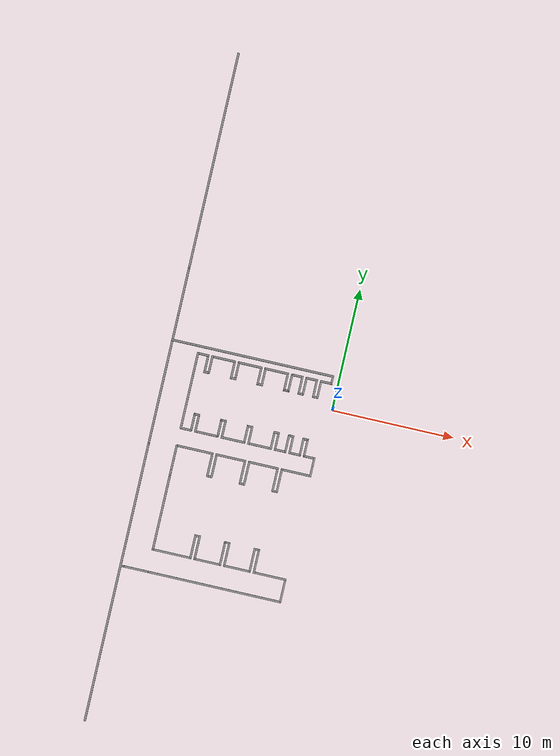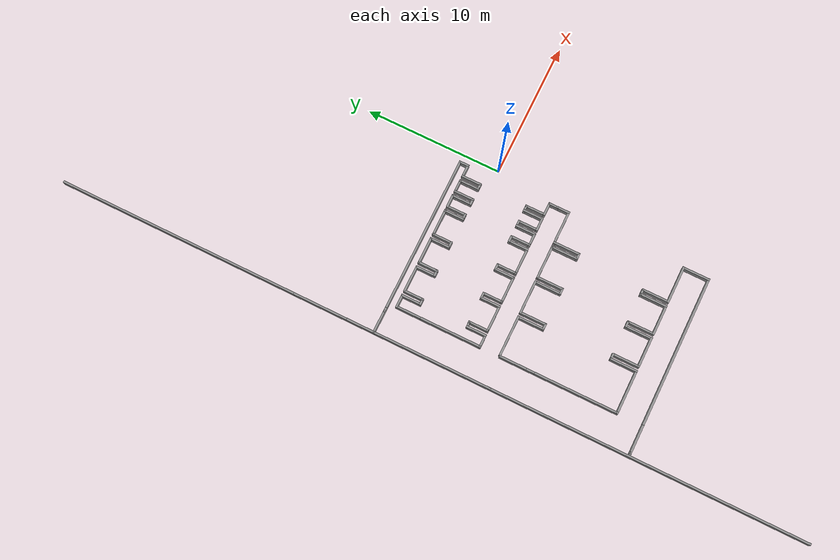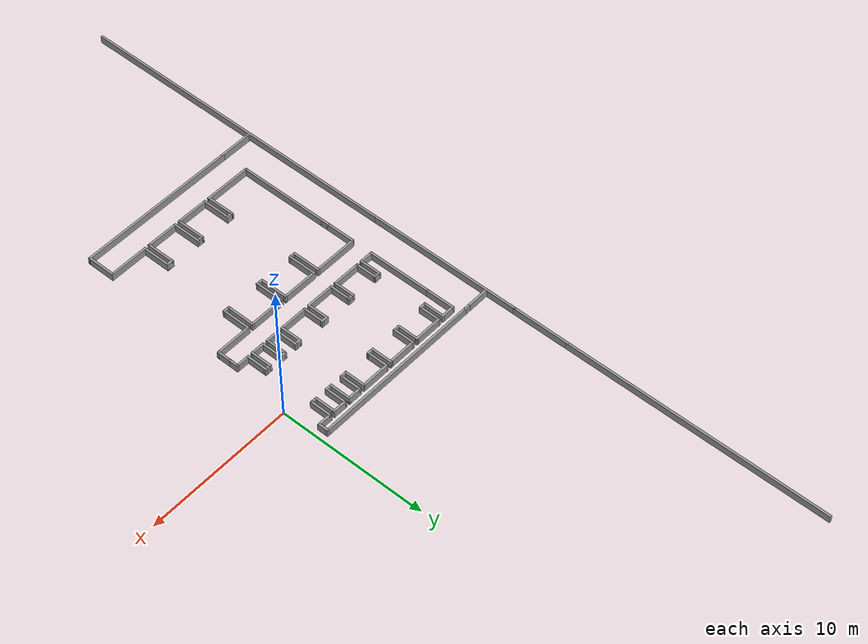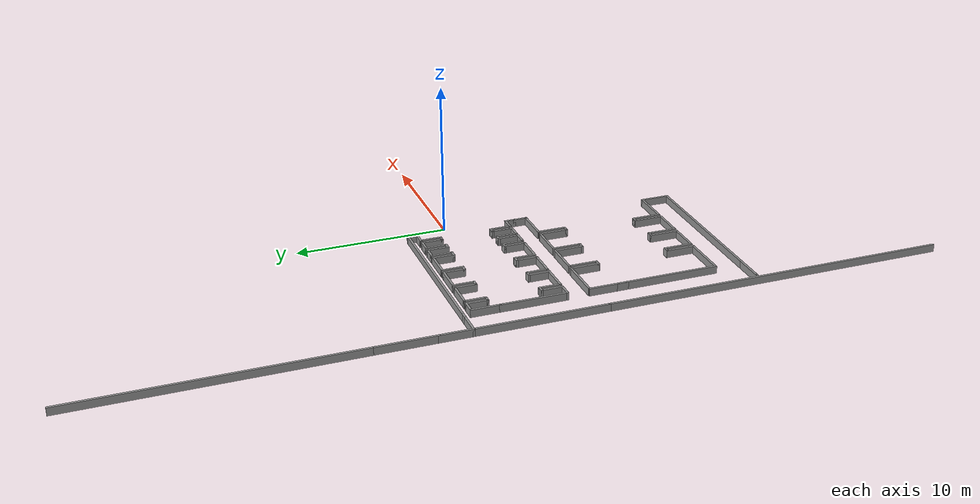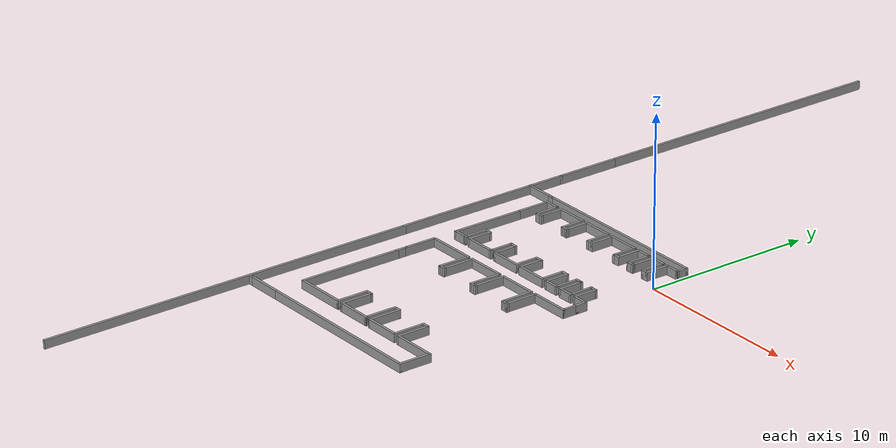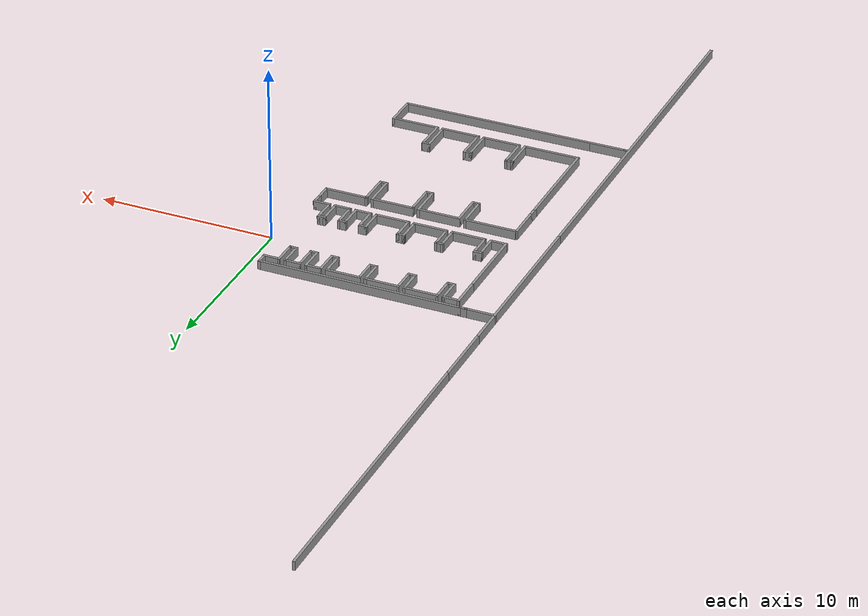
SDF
<?xml version='1.0'?>
<sdf version='1.6'>
  <model name='Dock3'>
    <pose frame=''>-6.9775 -1.135 0 0 -0 0</pose>
    <link name='Wall_0'>
      <collision name='Wall_0_Collision'>
        <geometry>
          <box>
            <size>1 0.15 0.5</size>
          </box>
        </geometry>
        <pose frame=''>0 0 0.00 0 -0 0</pose>
      </collision>
      <visual name='Wall_0_Visual'>
        <pose frame=''>0 0 0.00 0 -0 0</pose>
        <geometry>
          <box>
            <size>1 0.15 0.5</size>
          </box>
        </geometry>
        <material>
          <script>
            <uri>file://media/materials/scripts/gazebo.material</uri>
            <name>Gazebo/Grey</name>
          </script>
          <ambient>1 1 1 1</ambient>
        </material>
        <meta>
          <layer>0</layer>
        </meta>
      </visual>
      <pose frame=''>5.9725 -2.975 0 0 -0 3.14159</pose>
    </link>
    <link name='Wall_1'>
      <collision name='Wall_1_Collision'>
        <geometry>
          <box>
            <size>1.5 0.15 0.5</size>
          </box>
        </geometry>
        <pose frame=''>0 0 0.00 0 -0 0</pose>
      </collision>
      <visual name='Wall_1_Visual'>
        <pose frame=''>0 0 0.00 0 -0 0</pose>
        <geometry>
          <box>
            <size>1.5 0.15 0.5</size>
          </box>
        </geometry>
        <material>
          <script>
            <uri>file://media/materials/scripts/gazebo.material</uri>
            <name>Gazebo/Grey</name>
          </script>
          <ambient>1 1 1 1</ambient>
        </material>
        <meta>
          <layer>0</layer>
        </meta>
      </visual>
      <pose frame=''>5.5475 -2.3 0 0 -0 1.5708</pose>
    </link>
    <link name='Wall_10'>
      <collision name='Wall_10_Collision'>
        <geometry>
          <box>
            <size>0.5 0.15 0.5</size>
          </box>
        </geometry>
        <pose frame=''>0 0 0.00 0 -0 0</pose>
      </collision>
      <visual name='Wall_10_Visual'>
        <pose frame=''>0 0 0.00 0 -0 0</pose>
        <geometry>
          <box>
            <size>0.5 0.15 0.5</size>
          </box>
        </geometry>
        <material>
          <script>
            <uri>file://media/materials/scripts/gazebo.material</uri>
            <name>Gazebo/Grey</name>
          </script>
          <ambient>1 1 1 1</ambient>
        </material>
        <meta>
          <layer>0</layer>
        </meta>
      </visual>
      <pose frame=''>2.9725 -1.625 0 0 -0 3.14159</pose>
    </link>
    <link name='Wall_100'>
      <collision name='Wall_100_Collision'>
        <geometry>
          <box>
            <size>2 0.15 0.5</size>
          </box>
        </geometry>
        <pose frame=''>0 0 0.00 0 -0 0</pose>
      </collision>
      <visual name='Wall_100_Visual'>
        <pose frame=''>0 0 0.00 0 -0 0</pose>
        <geometry>
          <box>
            <size>2 0.15 0.5</size>
          </box>
        </geometry>
        <material>
          <script>
            <uri>file://media/materials/scripts/gazebo.material</uri>
            <name>Gazebo/Grey</name>
          </script>
          <ambient>1 1 1 1</ambient>
        </material>
        <meta>
          <layer>0</layer>
        </meta>
      </visual>
      <pose frame=''>1.3475 -5.35 0 0 -0 -1.5708</pose>
    </link>
    <link name='Wall_101'>
      <collision name='Wall_101_Collision'>
        <geometry>
          <box>
            <size>0.5 0.15 0.5</size>
          </box>
        </geometry>
        <pose frame=''>0 0 0.00 0 -0 0</pose>
      </collision>
      <visual name='Wall_101_Visual'>
        <pose frame=''>0 0 0.00 0 -0 0</pose>
        <geometry>
          <box>
            <size>0.5 0.15 0.5</size>
          </box>
        </geometry>
        <material>
          <script>
            <uri>file://media/materials/scripts/gazebo.material</uri>
            <name>Gazebo/Grey</name>
          </script>
          <ambient>1 1 1 1</ambient>
        </material>
        <meta>
          <layer>0</layer>
        </meta>
      </visual>
      <pose frame=''>1.1725 -6.275 0 0 -0 3.14159</pose>
    </link>
    <link name='Wall_102'>
      <collision name='Wall_102_Collision'>
        <geometry>
          <box>
            <size>2 0.15 0.5</size>
          </box>
        </geometry>
        <pose frame=''>0 0 0.00 0 -0 0</pose>
      </collision>
      <visual name='Wall_102_Visual'>
        <pose frame=''>0 0 0.00 0 -0 0</pose>
        <geometry>
          <box>
            <size>2 0.15 0.5</size>
          </box>
        </geometry>
        <material>
          <script>
            <uri>file://media/materials/scripts/gazebo.material</uri>
            <name>Gazebo/Grey</name>
          </script>
          <ambient>1 1 1 1</ambient>
        </material>
        <meta>
          <layer>0</layer>
        </meta>
      </visual>
      <pose frame=''>0.997501 -5.35 0 0 -0 1.5708</pose>
    </link>
    <link name='Wall_103'>
      <collision name='Wall_103_Collision'>
        <geometry>
          <box>
            <size>2.5 0.15 0.5</size>
          </box>
        </geometry>
        <pose frame=''>0 0 0.00 0 -0 0</pose>
      </collision>
      <visual name='Wall_103_Visual'>
        <pose frame=''>0 0 0.00 0 -0 0</pose>
        <geometry>
          <box>
            <size>2.5 0.15 0.5</size>
          </box>
        </geometry>
        <material>
          <script>
            <uri>file://media/materials/scripts/gazebo.material</uri>
            <name>Gazebo/Grey</name>
          </script>
          <ambient>1 1 1 1</ambient>
        </material>
        <meta>
          <layer>0</layer>
        </meta>
      </visual>
      <pose frame=''>-0.177499 -4.425 0 0 -0 3.14159</pose>
    </link>
    <link name='Wall_104'>
      <collision name='Wall_104_Collision'>
        <geometry>
          <box>
            <size>2 0.15 0.5</size>
          </box>
        </geometry>
        <pose frame=''>0 0 0.00 0 -0 0</pose>
      </collision>
      <visual name='Wall_104_Visual'>
        <pose frame=''>0 0 0.00 0 -0 0</pose>
        <geometry>
          <box>
            <size>2 0.15 0.5</size>
          </box>
        </geometry>
        <material>
          <script>
            <uri>file://media/materials/scripts/gazebo.material</uri>
            <name>Gazebo/Grey</name>
          </script>
          <ambient>1 1 1 1</ambient>
        </material>
        <meta>
          <layer>0</layer>
        </meta>
      </visual>
      <pose frame=''>-1.3525 -5.35 0 0 -0 -1.5708</pose>
    </link>
    <link name='Wall_105'>
      <collision name='Wall_105_Collision'>
        <geometry>
          <box>
            <size>0.5 0.15 0.5</size>
          </box>
        </geometry>
        <pose frame=''>0 0 0.00 0 -0 0</pose>
      </collision>
      <visual name='Wall_105_Visual'>
        <pose frame=''>0 0 0.00 0 -0 0</pose>
        <geometry>
          <box>
            <size>0.5 0.15 0.5</size>
          </box>
        </geometry>
        <material>
          <script>
            <uri>file://media/materials/scripts/gazebo.material</uri>
            <name>Gazebo/Grey</name>
          </script>
          <ambient>1 1 1 1</ambient>
        </material>
        <meta>
          <layer>0</layer>
        </meta>
      </visual>
      <pose frame=''>-1.5275 -6.275 0 0 -0 3.14159</pose>
    </link>
    <link name='Wall_106'>
      <collision name='Wall_106_Collision'>
        <geometry>
          <box>
            <size>2 0.15 0.5</size>
          </box>
        </geometry>
        <pose frame=''>0 0 0.00 0 -0 0</pose>
      </collision>
      <visual name='Wall_106_Visual'>
        <pose frame=''>0 0 0.00 0 -0 0</pose>
        <geometry>
          <box>
            <size>2 0.15 0.5</size>
          </box>
        </geometry>
        <material>
          <script>
            <uri>file://media/materials/scripts/gazebo.material</uri>
            <name>Gazebo/Grey</name>
          </script>
          <ambient>1 1 1 1</ambient>
        </material>
        <meta>
          <layer>0</layer>
        </meta>
      </visual>
      <pose frame=''>-1.7025 -5.35 0 0 -0 1.5708</pose>
    </link>
    <link name='Wall_11'>
      <collision name='Wall_11_Collision'>
        <geometry>
          <box>
            <size>1.5 0.15 0.5</size>
          </box>
        </geometry>
        <pose frame=''>0 0 0.00 0 -0 0</pose>
      </collision>
      <visual name='Wall_11_Visual'>
        <pose frame=''>0 0 0.00 0 -0 0</pose>
        <geometry>
          <box>
            <size>1.5 0.15 0.5</size>
          </box>
        </geometry>
        <material>
          <script>
            <uri>file://media/materials/scripts/gazebo.material</uri>
            <name>Gazebo/Grey</name>
          </script>
          <ambient>1 1 1 1</ambient>
        </material>
        <meta>
          <layer>0</layer>
        </meta>
      </visual>
      <pose frame=''>2.7975 -2.3 0 0 -0 -1.5708</pose>
    </link>
    <link name='Wall_112'>
      <collision name='Wall_112_Collision'>
        <geometry>
          <box>
            <size>3 0.15 0.5</size>
          </box>
        </geometry>
        <pose frame=''>0 0 0.00 0 -0 0</pose>
      </collision>
      <visual name='Wall_112_Visual'>
        <pose frame=''>0 0 0.00 0 -0 0</pose>
        <geometry>
          <box>
            <size>3 0.15 0.5</size>
          </box>
        </geometry>
        <material>
          <script>
            <uri>file://media/materials/scripts/gazebo.material</uri>
            <name>Gazebo/Grey</name>
          </script>
          <ambient>1 1 1 1</ambient>
        </material>
        <meta>
          <layer>0</layer>
        </meta>
      </visual>
      <pose frame=''>-3.1275 -4.425 0 0 -0 3.14159</pose>
    </link>
    <link name='Wall_114'>
      <collision name='Wall_114_Collision'>
        <geometry>
          <box>
            <size>0.75 0.15 0.5</size>
          </box>
        </geometry>
        <pose frame=''>0 0 0.00 0 -0 0</pose>
      </collision>
      <visual name='Wall_114_Visual'>
        <pose frame=''>0 0 0.00 0 -0 0</pose>
        <geometry>
          <box>
            <size>0.75 0.15 0.5</size>
          </box>
        </geometry>
        <material>
          <script>
            <uri>file://media/materials/scripts/gazebo.material</uri>
            <name>Gazebo/Grey</name>
          </script>
          <ambient>1 1 1 1</ambient>
        </material>
        <meta>
          <layer>0</layer>
        </meta>
      </visual>
      <pose frame=''>-4.6525 -6.625 0 0 -0 -1.5708</pose>
    </link>
    <link name='Wall_116'>
      <collision name='Wall_116_Collision'>
        <geometry>
          <box>
            <size>2 0.15 0.5</size>
          </box>
        </geometry>
        <pose frame=''>0 0 0.00 0 -0 0</pose>
      </collision>
      <visual name='Wall_116_Visual'>
        <pose frame=''>0 0 0.00 0 -0 0</pose>
        <geometry>
          <box>
            <size>2 0.15 0.5</size>
          </box>
        </geometry>
        <material>
          <script>
            <uri>file://media/materials/scripts/gazebo.material</uri>
            <name>Gazebo/Grey</name>
          </script>
          <ambient>1 1 1 1</ambient>
        </material>
        <meta>
          <layer>0</layer>
        </meta>
      </visual>
      <pose frame=''>-4.6525 -5.4 0 0 -0 1.5708</pose>
    </link>
    <link name='Wall_118'>
      <collision name='Wall_118_Collision'>
        <geometry>
          <box>
            <size>6.25 0.15 0.5</size>
          </box>
        </geometry>
        <pose frame=''>0 0 0.00 0 -0 0</pose>
      </collision>
      <visual name='Wall_118_Visual'>
        <pose frame=''>0 0 0.00 0 -0 0</pose>
        <geometry>
          <box>
            <size>6.25 0.15 0.5</size>
          </box>
        </geometry>
        <material>
          <script>
            <uri>file://media/materials/scripts/gazebo.material</uri>
            <name>Gazebo/Grey</name>
          </script>
          <ambient>1 1 1 1</ambient>
        </material>
        <meta>
          <layer>0</layer>
        </meta>
      </visual>
      <pose frame=''>-4.6525 -9.975 0 0 -0 -1.5708</pose>
    </link>
    <link name='Wall_119'>
      <collision name='Wall_119_Collision'>
        <geometry>
          <box>
            <size>3.25 0.15 0.5</size>
          </box>
        </geometry>
        <pose frame=''>0 0 0.00 0 -0 0</pose>
      </collision>
      <visual name='Wall_119_Visual'>
        <pose frame=''>0 0 0.00 0 -0 0</pose>
        <geometry>
          <box>
            <size>3.25 0.15 0.5</size>
          </box>
        </geometry>
        <material>
          <script>
            <uri>file://media/materials/scripts/gazebo.material</uri>
            <name>Gazebo/Grey</name>
          </script>
          <ambient>1 1 1 1</ambient>
        </material>
        <meta>
          <layer>0</layer>
        </meta>
      </visual>
      <pose frame=''>-3.1025 -13.025 0 0 -0 0</pose>
    </link>
    <link name='Wall_12'>
      <collision name='Wall_12_Collision'>
        <geometry>
          <box>
            <size>2 0.15 0.5</size>
          </box>
        </geometry>
        <pose frame=''>0 0 0.00 0 -0 0</pose>
      </collision>
      <visual name='Wall_12_Visual'>
        <pose frame=''>0 0 0.00 0 -0 0</pose>
        <geometry>
          <box>
            <size>2 0.15 0.5</size>
          </box>
        </geometry>
        <material>
          <script>
            <uri>file://media/materials/scripts/gazebo.material</uri>
            <name>Gazebo/Grey</name>
          </script>
          <ambient>1 1 1 1</ambient>
        </material>
        <meta>
          <layer>0</layer>
        </meta>
      </visual>
      <pose frame=''>1.8725 -2.975 0 0 -0 3.14159</pose>
    </link>
    <link name='Wall_120'>
      <collision name='Wall_120_Collision'>
        <geometry>
          <box>
            <size>2 0.15 0.5</size>
          </box>
        </geometry>
        <pose frame=''>0 0 0.00 0 -0 0</pose>
      </collision>
      <visual name='Wall_120_Visual'>
        <pose frame=''>0 0 0.00 0 -0 0</pose>
        <geometry>
          <box>
            <size>2 0.15 0.5</size>
          </box>
        </geometry>
        <material>
          <script>
            <uri>file://media/materials/scripts/gazebo.material</uri>
            <name>Gazebo/Grey</name>
          </script>
          <ambient>1 1 1 1</ambient>
        </material>
        <meta>
          <layer>0</layer>
        </meta>
      </visual>
      <pose frame=''>-1.5525 -12.1 0 0 -0 1.5708</pose>
    </link>
    <link name='Wall_123'>
      <collision name='Wall_123_Collision'>
        <geometry>
          <box>
            <size>0.15 0.15 0.5</size>
          </box>
        </geometry>
        <pose frame=''>0 0 0.00 0 -0 0</pose>
      </collision>
      <visual name='Wall_123_Visual'>
        <pose frame=''>0 0 0.00 0 -0 0</pose>
        <geometry>
          <box>
            <size>0.15 0.15 0.5</size>
          </box>
        </geometry>
        <material>
          <script>
            <uri>file://media/materials/scripts/gazebo.material</uri>
            <name>Gazebo/Grey</name>
          </script>
          <ambient>1 1 1 1</ambient>
        </material>
        <meta>
          <layer>0</layer>
        </meta>
      </visual>
      <pose frame=''>-1.5525 -11.175 0 0 -0 0</pose>
    </link>
    <link name='Wall_125'>
      <collision name='Wall_125_Collision'>
        <geometry>
          <box>
            <size>0.5 0.15 0.5</size>
          </box>
        </geometry>
        <pose frame=''>0 0 0.00 0 -0 0</pose>
      </collision>
      <visual name='Wall_125_Visual'>
        <pose frame=''>0 0 0.00 0 -0 0</pose>
        <geometry>
          <box>
            <size>0.5 0.15 0.5</size>
          </box>
        </geometry>
        <material>
          <script>
            <uri>file://media/materials/scripts/gazebo.material</uri>
            <name>Gazebo/Grey</name>
          </script>
          <ambient>1 1 1 1</ambient>
        </material>
        <meta>
          <layer>0</layer>
        </meta>
      </visual>
      <pose frame=''>-1.3775 -11.175 0 0 -0 0</pose>
    </link>
    <link name='Wall_126'>
      <collision name='Wall_126_Collision'>
        <geometry>
          <box>
            <size>2 0.15 0.5</size>
          </box>
        </geometry>
        <pose frame=''>0 0 0.00 0 -0 0</pose>
      </collision>
      <visual name='Wall_126_Visual'>
        <pose frame=''>0 0 0.00 0 -0 0</pose>
        <geometry>
          <box>
            <size>2 0.15 0.5</size>
          </box>
        </geometry>
        <material>
          <script>
            <uri>file://media/materials/scripts/gazebo.material</uri>
            <name>Gazebo/Grey</name>
          </script>
          <ambient>1 1 1 1</ambient>
        </material>
        <meta>
          <layer>0</layer>
        </meta>
      </visual>
      <pose frame=''>-1.2025 -12.1 0 0 -0 -1.5708</pose>
    </link>
    <link name='Wall_127'>
      <collision name='Wall_127_Collision'>
        <geometry>
          <box>
            <size>2.25 0.15 0.5</size>
          </box>
        </geometry>
        <pose frame=''>0 0 0.00 0 -0 0</pose>
      </collision>
      <visual name='Wall_127_Visual'>
        <pose frame=''>0 0 0.00 0 -0 0</pose>
        <geometry>
          <box>
            <size>2.25 0.15 0.5</size>
          </box>
        </geometry>
        <material>
          <script>
            <uri>file://media/materials/scripts/gazebo.material</uri>
            <name>Gazebo/Grey</name>
          </script>
          <ambient>1 1 1 1</ambient>
        </material>
        <meta>
          <layer>0</layer>
        </meta>
      </visual>
      <pose frame=''>-0.152499 -13.025 0 0 -0 0</pose>
    </link>
    <link name='Wall_13'>
      <collision name='Wall_13_Collision'>
        <geometry>
          <box>
            <size>1.5 0.15 0.5</size>
          </box>
        </geometry>
        <pose frame=''>0 0 0.00 0 -0 0</pose>
      </collision>
      <visual name='Wall_13_Visual'>
        <pose frame=''>0 0 0.00 0 -0 0</pose>
        <geometry>
          <box>
            <size>1.5 0.15 0.5</size>
          </box>
        </geometry>
        <material>
          <script>
            <uri>file://media/materials/scripts/gazebo.material</uri>
            <name>Gazebo/Grey</name>
          </script>
          <ambient>1 1 1 1</ambient>
        </material>
        <meta>
          <layer>0</layer>
        </meta>
      </visual>
      <pose frame=''>0.947501 -2.3 0 0 -0 1.5708</pose>
    </link>
    <link name='Wall_130'>
      <collision name='Wall_130_Collision'>
        <geometry>
          <box>
            <size>2 0.15 0.5</size>
          </box>
        </geometry>
        <pose frame=''>0 0 0.00 0 -0 0</pose>
      </collision>
      <visual name='Wall_130_Visual'>
        <pose frame=''>0 0 0.00 0 -0 0</pose>
        <geometry>
          <box>
            <size>2 0.15 0.5</size>
          </box>
        </geometry>
        <material>
          <script>
            <uri>file://media/materials/scripts/gazebo.material</uri>
            <name>Gazebo/Grey</name>
          </script>
          <ambient>1 1 1 1</ambient>
        </material>
        <meta>
          <layer>0</layer>
        </meta>
      </visual>
      <pose frame=''>0.897501 -12.1 0 0 -0 1.5708</pose>
    </link>
    <link name='Wall_131'>
      <collision name='Wall_131_Collision'>
        <geometry>
          <box>
            <size>0.5 0.15 0.5</size>
          </box>
        </geometry>
        <pose frame=''>0 0 0.00 0 -0 0</pose>
      </collision>
      <visual name='Wall_131_Visual'>
        <pose frame=''>0 0 0.00 0 -0 0</pose>
        <geometry>
          <box>
            <size>0.5 0.15 0.5</size>
          </box>
        </geometry>
        <material>
          <script>
            <uri>file://media/materials/scripts/gazebo.material</uri>
            <name>Gazebo/Grey</name>
          </script>
          <ambient>1 1 1 1</ambient>
        </material>
        <meta>
          <layer>0</layer>
        </meta>
      </visual>
      <pose frame=''>1.0725 -11.175 0 0 -0 0</pose>
    </link>
    <link name='Wall_132'>
      <collision name='Wall_132_Collision'>
        <geometry>
          <box>
            <size>2 0.15 0.5</size>
          </box>
        </geometry>
        <pose frame=''>0 0 0.00 0 -0 0</pose>
      </collision>
      <visual name='Wall_132_Visual'>
        <pose frame=''>0 0 0.00 0 -0 0</pose>
        <geometry>
          <box>
            <size>2 0.15 0.5</size>
          </box>
        </geometry>
        <material>
          <script>
            <uri>file://media/materials/scripts/gazebo.material</uri>
            <name>Gazebo/Grey</name>
          </script>
          <ambient>1 1 1 1</ambient>
        </material>
        <meta>
          <layer>0</layer>
        </meta>
      </visual>
      <pose frame=''>1.2475 -12.1 0 0 -0 -1.5708</pose>
    </link>
    <link name='Wall_133'>
      <collision name='Wall_133_Collision'>
        <geometry>
          <box>
            <size>2.25 0.15 0.5</size>
          </box>
        </geometry>
        <pose frame=''>0 0 0.00 0 -0 0</pose>
      </collision>
      <visual name='Wall_133_Visual'>
        <pose frame=''>0 0 0.00 0 -0 0</pose>
        <geometry>
          <box>
            <size>2.25 0.15 0.5</size>
          </box>
        </geometry>
        <material>
          <script>
            <uri>file://media/materials/scripts/gazebo.material</uri>
            <name>Gazebo/Grey</name>
          </script>
          <ambient>1 1 1 1</ambient>
        </material>
        <meta>
          <layer>0</layer>
        </meta>
      </visual>
      <pose frame=''>2.2975 -13.025 0 0 -0 0</pose>
    </link>
    <link name='Wall_134'>
      <collision name='Wall_134_Collision'>
        <geometry>
          <box>
            <size>2 0.15 0.5</size>
          </box>
        </geometry>
        <pose frame=''>0 0 0.00 0 -0 0</pose>
      </collision>
      <visual name='Wall_134_Visual'>
        <pose frame=''>0 0 0.00 0 -0 0</pose>
        <geometry>
          <box>
            <size>2 0.15 0.5</size>
          </box>
        </geometry>
        <material>
          <script>
            <uri>file://media/materials/scripts/gazebo.material</uri>
            <name>Gazebo/Grey</name>
          </script>
          <ambient>1 1 1 1</ambient>
        </material>
        <meta>
          <layer>0</layer>
        </meta>
      </visual>
      <pose frame=''>3.3475 -12.1 0 0 -0 1.5708</pose>
    </link>
    <link name='Wall_137'>
      <collision name='Wall_137_Collision'>
        <geometry>
          <box>
            <size>0.5 0.15 0.5</size>
          </box>
        </geometry>
        <pose frame=''>0 0 0.00 0 -0 0</pose>
      </collision>
      <visual name='Wall_137_Visual'>
        <pose frame=''>0 0 0.00 0 -0 0</pose>
        <geometry>
          <box>
            <size>0.5 0.15 0.5</size>
          </box>
        </geometry>
        <material>
          <script>
            <uri>file://media/materials/scripts/gazebo.material</uri>
            <name>Gazebo/Grey</name>
          </script>
          <ambient>1 1 1 1</ambient>
        </material>
        <meta>
          <layer>0</layer>
        </meta>
      </visual>
      <pose frame=''>3.5225 -11.175 0 0 -0 0</pose>
    </link>
    <link name='Wall_138'>
      <collision name='Wall_138_Collision'>
        <geometry>
          <box>
            <size>2 0.15 0.5</size>
          </box>
        </geometry>
        <pose frame=''>0 0 0.00 0 -0 0</pose>
      </collision>
      <visual name='Wall_138_Visual'>
        <pose frame=''>0 0 0.00 0 -0 0</pose>
        <geometry>
          <box>
            <size>2 0.15 0.5</size>
          </box>
        </geometry>
        <material>
          <script>
            <uri>file://media/materials/scripts/gazebo.material</uri>
            <name>Gazebo/Grey</name>
          </script>
          <ambient>1 1 1 1</ambient>
        </material>
        <meta>
          <layer>0</layer>
        </meta>
      </visual>
      <pose frame=''>3.6975 -12.1 0 0 -0 -1.5708</pose>
    </link>
    <link name='Wall_139'>
      <collision name='Wall_139_Collision'>
        <geometry>
          <box>
            <size>2.75 0.15 0.5</size>
          </box>
        </geometry>
        <pose frame=''>0 0 0.00 0 -0 0</pose>
      </collision>
      <visual name='Wall_139_Visual'>
        <pose frame=''>0 0 0.00 0 -0 0</pose>
        <geometry>
          <box>
            <size>2.75 0.15 0.5</size>
          </box>
        </geometry>
        <material>
          <script>
            <uri>file://media/materials/scripts/gazebo.material</uri>
            <name>Gazebo/Grey</name>
          </script>
          <ambient>1 1 1 1</ambient>
        </material>
        <meta>
          <layer>0</layer>
        </meta>
      </visual>
      <pose frame=''>4.9975 -13.025 0 0 -0 0</pose>
    </link>
    <link name='Wall_14'>
      <collision name='Wall_14_Collision'>
        <geometry>
          <box>
            <size>0.5 0.15 0.5</size>
          </box>
        </geometry>
        <pose frame=''>0 0 0.00 0 -0 0</pose>
      </collision>
      <visual name='Wall_14_Visual'>
        <pose frame=''>0 0 0.00 0 -0 0</pose>
        <geometry>
          <box>
            <size>0.5 0.15 0.5</size>
          </box>
        </geometry>
        <material>
          <script>
            <uri>file://media/materials/scripts/gazebo.material</uri>
            <name>Gazebo/Grey</name>
          </script>
          <ambient>1 1 1 1</ambient>
        </material>
        <meta>
          <layer>0</layer>
        </meta>
      </visual>
      <pose frame=''>0.772501 -1.625 0 0 -0 3.14159</pose>
    </link>
    <link name='Wall_141'>
      <collision name='Wall_141_Collision'>
        <geometry>
          <box>
            <size>2 0.15 0.5</size>
          </box>
        </geometry>
        <pose frame=''>0 0 0.00 0 -0 0</pose>
      </collision>
      <visual name='Wall_141_Visual'>
        <pose frame=''>0 0 0.00 0 -0 0</pose>
        <geometry>
          <box>
            <size>2 0.15 0.5</size>
          </box>
        </geometry>
        <material>
          <script>
            <uri>file://media/materials/scripts/gazebo.material</uri>
            <name>Gazebo/Grey</name>
          </script>
          <ambient>1 1 1 1</ambient>
        </material>
        <meta>
          <layer>0</layer>
        </meta>
      </visual>
      <pose frame=''>6.2975 -13.95 0 0 -0 -1.5708</pose>
    </link>
    <link name='Wall_142'>
      <collision name='Wall_142_Collision'>
        <geometry>
          <box>
            <size>11 0.15 0.5</size>
          </box>
        </geometry>
        <pose frame=''>0 0 0.00 0 -0 0</pose>
      </collision>
      <visual name='Wall_142_Visual'>
        <pose frame=''>0 0 0.00 0 -0 0</pose>
        <geometry>
          <box>
            <size>11 0.15 0.5</size>
          </box>
        </geometry>
        <material>
          <script>
            <uri>file://media/materials/scripts/gazebo.material</uri>
            <name>Gazebo/Grey</name>
          </script>
          <ambient>1 1 1 1</ambient>
        </material>
        <meta>
          <layer>0</layer>
        </meta>
      </visual>
      <pose frame=''>0.872501 -14.875 0 0 -0 3.14159</pose>
    </link>
    <link name='Wall_143'>
      <collision name='Wall_143_Collision'>
        <geometry>
          <box>
            <size>2.25 0.15 0.5</size>
          </box>
        </geometry>
        <pose frame=''>0 0 0.00 0 -0 0</pose>
      </collision>
      <visual name='Wall_143_Visual'>
        <pose frame=''>0 0 0.00 0 -0 0</pose>
        <geometry>
          <box>
            <size>2.25 0.15 0.5</size>
          </box>
        </geometry>
        <material>
          <script>
            <uri>file://media/materials/scripts/gazebo.material</uri>
            <name>Gazebo/Grey</name>
          </script>
          <ambient>1 1 1 1</ambient>
        </material>
        <meta>
          <layer>0</layer>
        </meta>
      </visual>
      <pose frame=''>-5.6025 -14.875 0 0 -0 3.14159</pose>
    </link>
    <link name='Wall_144'>
      <collision name='Wall_144_Collision'>
        <geometry>
          <box>
            <size>0.15 0.15 0.5</size>
          </box>
        </geometry>
        <pose frame=''>0 0 0.00 0 -0 0</pose>
      </collision>
      <visual name='Wall_144_Visual'>
        <pose frame=''>0 0 0.00 0 -0 0</pose>
        <geometry>
          <box>
            <size>0.15 0.15 0.5</size>
          </box>
        </geometry>
        <material>
          <script>
            <uri>file://media/materials/scripts/gazebo.material</uri>
            <name>Gazebo/Grey</name>
          </script>
          <ambient>1 1 1 1</ambient>
        </material>
        <meta>
          <layer>0</layer>
        </meta>
      </visual>
      <pose frame=''>-6.6525 -14.875 0 0 -0 0</pose>
    </link>
    <link name='Wall_146'>
      <collision name='Wall_146_Collision'>
        <geometry>
          <box>
            <size>0.25 0.15 0.5</size>
          </box>
        </geometry>
        <pose frame=''>0 0 0.00 0 -0 0</pose>
      </collision>
      <visual name='Wall_146_Visual'>
        <pose frame=''>0 0 0.00 0 -0 0</pose>
        <geometry>
          <box>
            <size>0.25 0.15 0.5</size>
          </box>
        </geometry>
        <material>
          <script>
            <uri>file://media/materials/scripts/gazebo.material</uri>
            <name>Gazebo/Grey</name>
          </script>
          <ambient>1 1 1 1</ambient>
        </material>
        <meta>
          <layer>0</layer>
        </meta>
      </visual>
      <pose frame=''>-6.7025 -14.875 0 0 -0 3.14159</pose>
    </link>
    <link name='Wall_15'>
      <collision name='Wall_15_Collision'>
        <geometry>
          <box>
            <size>1.5 0.15 0.5</size>
          </box>
        </geometry>
        <pose frame=''>0 0 0.00 0 -0 0</pose>
      </collision>
      <visual name='Wall_15_Visual'>
        <pose frame=''>0 0 0.00 0 -0 0</pose>
        <geometry>
          <box>
            <size>1.5 0.15 0.5</size>
          </box>
        </geometry>
        <material>
          <script>
            <uri>file://media/materials/scripts/gazebo.material</uri>
            <name>Gazebo/Grey</name>
          </script>
          <ambient>1 1 1 1</ambient>
        </material>
        <meta>
          <layer>0</layer>
        </meta>
      </visual>
      <pose frame=''>0.597501 -2.3 0 0 -0 -1.5708</pose>
    </link>
    <link name='Wall_17'>
      <collision name='Wall_17_Collision'>
        <geometry>
          <box>
            <size>2 0.15 0.5</size>
          </box>
        </geometry>
        <pose frame=''>0 0 0.00 0 -0 0</pose>
      </collision>
      <visual name='Wall_17_Visual'>
        <pose frame=''>0 0 0.00 0 -0 0</pose>
        <geometry>
          <box>
            <size>2 0.15 0.5</size>
          </box>
        </geometry>
        <material>
          <script>
            <uri>file://media/materials/scripts/gazebo.material</uri>
            <name>Gazebo/Grey</name>
          </script>
          <ambient>1 1 1 1</ambient>
        </material>
        <meta>
          <layer>0</layer>
        </meta>
      </visual>
      <pose frame=''>-0.327499 -2.975 0 0 -0 3.14159</pose>
    </link>
    <link name='Wall_18'>
      <collision name='Wall_18_Collision'>
        <geometry>
          <box>
            <size>1.5 0.15 0.5</size>
          </box>
        </geometry>
        <pose frame=''>0 0 0.00 0 -0 0</pose>
      </collision>
      <visual name='Wall_18_Visual'>
        <pose frame=''>0 0 0.00 0 -0 0</pose>
        <geometry>
          <box>
            <size>1.5 0.15 0.5</size>
          </box>
        </geometry>
        <material>
          <script>
            <uri>file://media/materials/scripts/gazebo.material</uri>
            <name>Gazebo/Grey</name>
          </script>
          <ambient>1 1 1 1</ambient>
        </material>
        <meta>
          <layer>0</layer>
        </meta>
      </visual>
      <pose frame=''>-1.2525 -2.3 0 0 -0 1.5708</pose>
    </link>
    <link name='Wall_19'>
      <collision name='Wall_19_Collision'>
        <geometry>
          <box>
            <size>0.5 0.15 0.5</size>
          </box>
        </geometry>
        <pose frame=''>0 0 0.00 0 -0 0</pose>
      </collision>
      <visual name='Wall_19_Visual'>
        <pose frame=''>0 0 0.00 0 -0 0</pose>
        <geometry>
          <box>
            <size>0.5 0.15 0.5</size>
          </box>
        </geometry>
        <material>
          <script>
            <uri>file://media/materials/scripts/gazebo.material</uri>
            <name>Gazebo/Grey</name>
          </script>
          <ambient>1 1 1 1</ambient>
        </material>
        <meta>
          <layer>0</layer>
        </meta>
      </visual>
      <pose frame=''>-1.4275 -1.625 0 0 -0 3.14159</pose>
    </link>
    <link name='Wall_2'>
      <collision name='Wall_2_Collision'>
        <geometry>
          <box>
            <size>0.5 0.15 0.5</size>
          </box>
        </geometry>
        <pose frame=''>0 0 0.00 0 -0 0</pose>
      </collision>
      <visual name='Wall_2_Visual'>
        <pose frame=''>0 0 0.00 0 -0 0</pose>
        <geometry>
          <box>
            <size>0.5 0.15 0.5</size>
          </box>
        </geometry>
        <material>
          <script>
            <uri>file://media/materials/scripts/gazebo.material</uri>
            <name>Gazebo/Grey</name>
          </script>
          <ambient>1 1 1 1</ambient>
        </material>
        <meta>
          <layer>0</layer>
        </meta>
      </visual>
      <pose frame=''>5.3725 -1.625 0 0 -0 3.14159</pose>
    </link>
    <link name='Wall_20'>
      <collision name='Wall_20_Collision'>
        <geometry>
          <box>
            <size>1.5 0.15 0.5</size>
          </box>
        </geometry>
        <pose frame=''>0 0 0.00 0 -0 0</pose>
      </collision>
      <visual name='Wall_20_Visual'>
        <pose frame=''>0 0 0.00 0 -0 0</pose>
        <geometry>
          <box>
            <size>1.5 0.15 0.5</size>
          </box>
        </geometry>
        <material>
          <script>
            <uri>file://media/materials/scripts/gazebo.material</uri>
            <name>Gazebo/Grey</name>
          </script>
          <ambient>1 1 1 1</ambient>
        </material>
        <meta>
          <layer>0</layer>
        </meta>
      </visual>
      <pose frame=''>-1.6025 -2.3 0 0 -0 -1.5708</pose>
    </link>
    <link name='Wall_21'>
      <collision name='Wall_21_Collision'>
        <geometry>
          <box>
            <size>2 0.15 0.5</size>
          </box>
        </geometry>
        <pose frame=''>0 0 0.00 0 -0 0</pose>
      </collision>
      <visual name='Wall_21_Visual'>
        <pose frame=''>0 0 0.00 0 -0 0</pose>
        <geometry>
          <box>
            <size>2 0.15 0.5</size>
          </box>
        </geometry>
        <material>
          <script>
            <uri>file://media/materials/scripts/gazebo.material</uri>
            <name>Gazebo/Grey</name>
          </script>
          <ambient>1 1 1 1</ambient>
        </material>
        <meta>
          <layer>0</layer>
        </meta>
      </visual>
      <pose frame=''>-2.5275 -2.975 0 0 -0 3.14159</pose>
    </link>
    <link name='Wall_22'>
      <collision name='Wall_22_Collision'>
        <geometry>
          <box>
            <size>1.5 0.15 0.5</size>
          </box>
        </geometry>
        <pose frame=''>0 0 0.00 0 -0 0</pose>
      </collision>
      <visual name='Wall_22_Visual'>
        <pose frame=''>0 0 0.00 0 -0 0</pose>
        <geometry>
          <box>
            <size>1.5 0.15 0.5</size>
          </box>
        </geometry>
        <material>
          <script>
            <uri>file://media/materials/scripts/gazebo.material</uri>
            <name>Gazebo/Grey</name>
          </script>
          <ambient>1 1 1 1</ambient>
        </material>
        <meta>
          <layer>0</layer>
        </meta>
      </visual>
      <pose frame=''>-3.4525 -2.3 0 0 -0 1.5708</pose>
    </link>
    <link name='Wall_23'>
      <collision name='Wall_23_Collision'>
        <geometry>
          <box>
            <size>0.5 0.15 0.5</size>
          </box>
        </geometry>
        <pose frame=''>0 0 0.00 0 -0 0</pose>
      </collision>
      <visual name='Wall_23_Visual'>
        <pose frame=''>0 0 0.00 0 -0 0</pose>
        <geometry>
          <box>
            <size>0.5 0.15 0.5</size>
          </box>
        </geometry>
        <material>
          <script>
            <uri>file://media/materials/scripts/gazebo.material</uri>
            <name>Gazebo/Grey</name>
          </script>
          <ambient>1 1 1 1</ambient>
        </material>
        <meta>
          <layer>0</layer>
        </meta>
      </visual>
      <pose frame=''>-3.6275 -1.625 0 0 -0 3.14159</pose>
    </link>
    <link name='Wall_24'>
      <collision name='Wall_24_Collision'>
        <geometry>
          <box>
            <size>1.5 0.15 0.5</size>
          </box>
        </geometry>
        <pose frame=''>0 0 0.00 0 -0 0</pose>
      </collision>
      <visual name='Wall_24_Visual'>
        <pose frame=''>0 0 0.00 0 -0 0</pose>
        <geometry>
          <box>
            <size>1.5 0.15 0.5</size>
          </box>
        </geometry>
        <material>
          <script>
            <uri>file://media/materials/scripts/gazebo.material</uri>
            <name>Gazebo/Grey</name>
          </script>
          <ambient>1 1 1 1</ambient>
        </material>
        <meta>
          <layer>0</layer>
        </meta>
      </visual>
      <pose frame=''>-3.8025 -2.3 0 0 -0 -1.5708</pose>
    </link>
    <link name='Wall_25'>
      <collision name='Wall_25_Collision'>
        <geometry>
          <box>
            <size>1 0.15 0.5</size>
          </box>
        </geometry>
        <pose frame=''>0 0 0.00 0 -0 0</pose>
      </collision>
      <visual name='Wall_25_Visual'>
        <pose frame=''>0 0 0.00 0 -0 0</pose>
        <geometry>
          <box>
            <size>1 0.15 0.5</size>
          </box>
        </geometry>
        <material>
          <script>
            <uri>file://media/materials/scripts/gazebo.material</uri>
            <name>Gazebo/Grey</name>
          </script>
          <ambient>1 1 1 1</ambient>
        </material>
        <meta>
          <layer>0</layer>
        </meta>
      </visual>
      <pose frame=''>-4.2275 -2.975 0 0 -0 3.14159</pose>
    </link>
    <link name='Wall_27'>
      <collision name='Wall_27_Collision'>
        <geometry>
          <box>
            <size>4.5 0.15 0.5</size>
          </box>
        </geometry>
        <pose frame=''>0 0 0.00 0 -0 0</pose>
      </collision>
      <visual name='Wall_27_Visual'>
        <pose frame=''>0 0 0.00 0 -0 0</pose>
        <geometry>
          <box>
            <size>4.5 0.15 0.5</size>
          </box>
        </geometry>
        <material>
          <script>
            <uri>file://media/materials/scripts/gazebo.material</uri>
            <name>Gazebo/Grey</name>
          </script>
          <ambient>1 1 1 1</ambient>
        </material>
        <meta>
          <layer>0</layer>
        </meta>
      </visual>
      <pose frame=''>-4.6525 -0.800002 0 0 -0 1.5708</pose>
    </link>
    <link name='Wall_3'>
      <collision name='Wall_3_Collision'>
        <geometry>
          <box>
            <size>1.5 0.15 0.5</size>
          </box>
        </geometry>
        <pose frame=''>0 0 0.00 0 -0 0</pose>
      </collision>
      <visual name='Wall_3_Visual'>
        <pose frame=''>0 0 0.00 0 -0 0</pose>
        <geometry>
          <box>
            <size>1.5 0.15 0.5</size>
          </box>
        </geometry>
        <material>
          <script>
            <uri>file://media/materials/scripts/gazebo.material</uri>
            <name>Gazebo/Grey</name>
          </script>
          <ambient>1 1 1 1</ambient>
        </material>
        <meta>
          <layer>0</layer>
        </meta>
      </visual>
      <pose frame=''>5.1975 -2.3 0 0 -0 -1.5708</pose>
    </link>
    <link name='Wall_30'>
      <collision name='Wall_30_Collision'>
        <geometry>
          <box>
            <size>2 0.15 0.5</size>
          </box>
        </geometry>
        <pose frame=''>0 0 0.00 0 -0 0</pose>
      </collision>
      <visual name='Wall_30_Visual'>
        <pose frame=''>0 0 0.00 0 -0 0</pose>
        <geometry>
          <box>
            <size>2 0.15 0.5</size>
          </box>
        </geometry>
        <material>
          <script>
            <uri>file://media/materials/scripts/gazebo.material</uri>
            <name>Gazebo/Grey</name>
          </script>
          <ambient>1 1 1 1</ambient>
        </material>
        <meta>
          <layer>0</layer>
        </meta>
      </visual>
      <pose frame=''>-4.6525 2.3 0 0 -0 1.5708</pose>
    </link>
    <link name='Wall_33'>
      <collision name='Wall_33_Collision'>
        <geometry>
          <box>
            <size>1 0.15 0.5</size>
          </box>
        </geometry>
        <pose frame=''>0 0 0.00 0 -0 0</pose>
      </collision>
      <visual name='Wall_33_Visual'>
        <pose frame=''>0 0 0.00 0 -0 0</pose>
        <geometry>
          <box>
            <size>1 0.15 0.5</size>
          </box>
        </geometry>
        <material>
          <script>
            <uri>file://media/materials/scripts/gazebo.material</uri>
            <name>Gazebo/Grey</name>
          </script>
          <ambient>1 1 1 1</ambient>
        </material>
        <meta>
          <layer>0</layer>
        </meta>
      </visual>
      <pose frame=''>-4.2275 3.225 0 0 -0 0</pose>
    </link>
    <link name='Wall_34'>
      <collision name='Wall_34_Collision'>
        <geometry>
          <box>
            <size>1.5 0.15 0.5</size>
          </box>
        </geometry>
        <pose frame=''>0 0 0.00 0 -0 0</pose>
      </collision>
      <visual name='Wall_34_Visual'>
        <pose frame=''>0 0 0.00 0 -0 0</pose>
        <geometry>
          <box>
            <size>1.5 0.15 0.5</size>
          </box>
        </geometry>
        <material>
          <script>
            <uri>file://media/materials/scripts/gazebo.material</uri>
            <name>Gazebo/Grey</name>
          </script>
          <ambient>1 1 1 1</ambient>
        </material>
        <meta>
          <layer>0</layer>
        </meta>
      </visual>
      <pose frame=''>-3.8025 2.55 0 0 -0 -1.5708</pose>
    </link>
    <link name='Wall_35'>
      <collision name='Wall_35_Collision'>
        <geometry>
          <box>
            <size>0.5 0.15 0.5</size>
          </box>
        </geometry>
        <pose frame=''>0 0 0.00 0 -0 0</pose>
      </collision>
      <visual name='Wall_35_Visual'>
        <pose frame=''>0 0 0.00 0 -0 0</pose>
        <geometry>
          <box>
            <size>0.5 0.15 0.5</size>
          </box>
        </geometry>
        <material>
          <script>
            <uri>file://media/materials/scripts/gazebo.material</uri>
            <name>Gazebo/Grey</name>
          </script>
          <ambient>1 1 1 1</ambient>
        </material>
        <meta>
          <layer>0</layer>
        </meta>
      </visual>
      <pose frame=''>-3.6275 1.875 0 0 -0 0</pose>
    </link>
    <link name='Wall_36'>
      <collision name='Wall_36_Collision'>
        <geometry>
          <box>
            <size>1.5 0.15 0.5</size>
          </box>
        </geometry>
        <pose frame=''>0 0 0.00 0 -0 0</pose>
      </collision>
      <visual name='Wall_36_Visual'>
        <pose frame=''>0 0 0.00 0 -0 0</pose>
        <geometry>
          <box>
            <size>1.5 0.15 0.5</size>
          </box>
        </geometry>
        <material>
          <script>
            <uri>file://media/materials/scripts/gazebo.material</uri>
            <name>Gazebo/Grey</name>
          </script>
          <ambient>1 1 1 1</ambient>
        </material>
        <meta>
          <layer>0</layer>
        </meta>
      </visual>
      <pose frame=''>-3.4525 2.55 0 0 -0 1.5708</pose>
    </link>
    <link name='Wall_37'>
      <collision name='Wall_37_Collision'>
        <geometry>
          <box>
            <size>2 0.15 0.5</size>
          </box>
        </geometry>
        <pose frame=''>0 0 0.00 0 -0 0</pose>
      </collision>
      <visual name='Wall_37_Visual'>
        <pose frame=''>0 0 0.00 0 -0 0</pose>
        <geometry>
          <box>
            <size>2 0.15 0.5</size>
          </box>
        </geometry>
        <material>
          <script>
            <uri>file://media/materials/scripts/gazebo.material</uri>
            <name>Gazebo/Grey</name>
          </script>
          <ambient>1 1 1 1</ambient>
        </material>
        <meta>
          <layer>0</layer>
        </meta>
      </visual>
      <pose frame=''>-2.5275 3.225 0 0 -0 0</pose>
    </link>
    <link name='Wall_38'>
      <collision name='Wall_38_Collision'>
        <geometry>
          <box>
            <size>1.5 0.15 0.5</size>
          </box>
        </geometry>
        <pose frame=''>0 0 0.00 0 -0 0</pose>
      </collision>
      <visual name='Wall_38_Visual'>
        <pose frame=''>0 0 0.00 0 -0 0</pose>
        <geometry>
          <box>
            <size>1.5 0.15 0.5</size>
          </box>
        </geometry>
        <material>
          <script>
            <uri>file://media/materials/scripts/gazebo.material</uri>
            <name>Gazebo/Grey</name>
          </script>
          <ambient>1 1 1 1</ambient>
        </material>
        <meta>
          <layer>0</layer>
        </meta>
      </visual>
      <pose frame=''>-1.6025 2.55 0 0 -0 -1.5708</pose>
    </link>
    <link name='Wall_39'>
      <collision name='Wall_39_Collision'>
        <geometry>
          <box>
            <size>0.5 0.15 0.5</size>
          </box>
        </geometry>
        <pose frame=''>0 0 0.00 0 -0 0</pose>
      </collision>
      <visual name='Wall_39_Visual'>
        <pose frame=''>0 0 0.00 0 -0 0</pose>
        <geometry>
          <box>
            <size>0.5 0.15 0.5</size>
          </box>
        </geometry>
        <material>
          <script>
            <uri>file://media/materials/scripts/gazebo.material</uri>
            <name>Gazebo/Grey</name>
          </script>
          <ambient>1 1 1 1</ambient>
        </material>
        <meta>
          <layer>0</layer>
        </meta>
      </visual>
      <pose frame=''>-1.4275 1.875 0 0 -0 0</pose>
    </link>
    <link name='Wall_4'>
      <collision name='Wall_4_Collision'>
        <geometry>
          <box>
            <size>1 0.15 0.5</size>
          </box>
        </geometry>
        <pose frame=''>0 0 0.00 0 -0 0</pose>
      </collision>
      <visual name='Wall_4_Visual'>
        <pose frame=''>0 0 0.00 0 -0 0</pose>
        <geometry>
          <box>
            <size>1 0.15 0.5</size>
          </box>
        </geometry>
        <material>
          <script>
            <uri>file://media/materials/scripts/gazebo.material</uri>
            <name>Gazebo/Grey</name>
          </script>
          <ambient>1 1 1 1</ambient>
        </material>
        <meta>
          <layer>0</layer>
        </meta>
      </visual>
      <pose frame=''>4.7725 -2.975 0 0 -0 3.14159</pose>
    </link>
    <link name='Wall_40'>
      <collision name='Wall_40_Collision'>
        <geometry>
          <box>
            <size>1.5 0.15 0.5</size>
          </box>
        </geometry>
        <pose frame=''>0 0 0.00 0 -0 0</pose>
      </collision>
      <visual name='Wall_40_Visual'>
        <pose frame=''>0 0 0.00 0 -0 0</pose>
        <geometry>
          <box>
            <size>1.5 0.15 0.5</size>
          </box>
        </geometry>
        <material>
          <script>
            <uri>file://media/materials/scripts/gazebo.material</uri>
            <name>Gazebo/Grey</name>
          </script>
          <ambient>1 1 1 1</ambient>
        </material>
        <meta>
          <layer>0</layer>
        </meta>
      </visual>
      <pose frame=''>-1.2525 2.55 0 0 -0 1.5708</pose>
    </link>
    <link name='Wall_41'>
      <collision name='Wall_41_Collision'>
        <geometry>
          <box>
            <size>2 0.15 0.5</size>
          </box>
        </geometry>
        <pose frame=''>0 0 0.00 0 -0 0</pose>
      </collision>
      <visual name='Wall_41_Visual'>
        <pose frame=''>0 0 0.00 0 -0 0</pose>
        <geometry>
          <box>
            <size>2 0.15 0.5</size>
          </box>
        </geometry>
        <material>
          <script>
            <uri>file://media/materials/scripts/gazebo.material</uri>
            <name>Gazebo/Grey</name>
          </script>
          <ambient>1 1 1 1</ambient>
        </material>
        <meta>
          <layer>0</layer>
        </meta>
      </visual>
      <pose frame=''>-0.327499 3.225 0 0 -0 0</pose>
    </link>
    <link name='Wall_42'>
      <collision name='Wall_42_Collision'>
        <geometry>
          <box>
            <size>1.5 0.15 0.5</size>
          </box>
        </geometry>
        <pose frame=''>0 0 0.00 0 -0 0</pose>
      </collision>
      <visual name='Wall_42_Visual'>
        <pose frame=''>0 0 0.00 0 -0 0</pose>
        <geometry>
          <box>
            <size>1.5 0.15 0.5</size>
          </box>
        </geometry>
        <material>
          <script>
            <uri>file://media/materials/scripts/gazebo.material</uri>
            <name>Gazebo/Grey</name>
          </script>
          <ambient>1 1 1 1</ambient>
        </material>
        <meta>
          <layer>0</layer>
        </meta>
      </visual>
      <pose frame=''>0.597501 2.55 0 0 -0 -1.5708</pose>
    </link>
    <link name='Wall_43'>
      <collision name='Wall_43_Collision'>
        <geometry>
          <box>
            <size>0.5 0.15 0.5</size>
          </box>
        </geometry>
        <pose frame=''>0 0 0.00 0 -0 0</pose>
      </collision>
      <visual name='Wall_43_Visual'>
        <pose frame=''>0 0 0.00 0 -0 0</pose>
        <geometry>
          <box>
            <size>0.5 0.15 0.5</size>
          </box>
        </geometry>
        <material>
          <script>
            <uri>file://media/materials/scripts/gazebo.material</uri>
            <name>Gazebo/Grey</name>
          </script>
          <ambient>1 1 1 1</ambient>
        </material>
        <meta>
          <layer>0</layer>
        </meta>
      </visual>
      <pose frame=''>0.772501 1.875 0 0 -0 0</pose>
    </link>
    <link name='Wall_45'>
      <collision name='Wall_45_Collision'>
        <geometry>
          <box>
            <size>1.5 0.15 0.5</size>
          </box>
        </geometry>
        <pose frame=''>0 0 0.00 0 -0 0</pose>
      </collision>
      <visual name='Wall_45_Visual'>
        <pose frame=''>0 0 0.00 0 -0 0</pose>
        <geometry>
          <box>
            <size>1.5 0.15 0.5</size>
          </box>
        </geometry>
        <material>
          <script>
            <uri>file://media/materials/scripts/gazebo.material</uri>
            <name>Gazebo/Grey</name>
          </script>
          <ambient>1 1 1 1</ambient>
        </material>
        <meta>
          <layer>0</layer>
        </meta>
      </visual>
      <pose frame=''>0.947501 2.55 0 0 -0 1.5708</pose>
    </link>
    <link name='Wall_47'>
      <collision name='Wall_47_Collision'>
        <geometry>
          <box>
            <size>2 0.15 0.5</size>
          </box>
        </geometry>
        <pose frame=''>0 0 0.00 0 -0 0</pose>
      </collision>
      <visual name='Wall_47_Visual'>
        <pose frame=''>0 0 0.00 0 -0 0</pose>
        <geometry>
          <box>
            <size>2 0.15 0.5</size>
          </box>
        </geometry>
        <material>
          <script>
            <uri>file://media/materials/scripts/gazebo.material</uri>
            <name>Gazebo/Grey</name>
          </script>
          <ambient>1 1 1 1</ambient>
        </material>
        <meta>
          <layer>0</layer>
        </meta>
      </visual>
      <pose frame=''>1.8725 3.225 0 0 -0 0</pose>
    </link>
    <link name='Wall_48'>
      <collision name='Wall_48_Collision'>
        <geometry>
          <box>
            <size>1.5 0.15 0.5</size>
          </box>
        </geometry>
        <pose frame=''>0 0 0.00 0 -0 0</pose>
      </collision>
      <visual name='Wall_48_Visual'>
        <pose frame=''>0 0 0.00 0 -0 0</pose>
        <geometry>
          <box>
            <size>1.5 0.15 0.5</size>
          </box>
        </geometry>
        <material>
          <script>
            <uri>file://media/materials/scripts/gazebo.material</uri>
            <name>Gazebo/Grey</name>
          </script>
          <ambient>1 1 1 1</ambient>
        </material>
        <meta>
          <layer>0</layer>
        </meta>
      </visual>
      <pose frame=''>2.7975 2.55 0 0 -0 -1.5708</pose>
    </link>
    <link name='Wall_49'>
      <collision name='Wall_49_Collision'>
        <geometry>
          <box>
            <size>0.5 0.15 0.5</size>
          </box>
        </geometry>
        <pose frame=''>0 0 0.00 0 -0 0</pose>
      </collision>
      <visual name='Wall_49_Visual'>
        <pose frame=''>0 0 0.00 0 -0 0</pose>
        <geometry>
          <box>
            <size>0.5 0.15 0.5</size>
          </box>
        </geometry>
        <material>
          <script>
            <uri>file://media/materials/scripts/gazebo.material</uri>
            <name>Gazebo/Grey</name>
          </script>
          <ambient>1 1 1 1</ambient>
        </material>
        <meta>
          <layer>0</layer>
        </meta>
      </visual>
      <pose frame=''>2.9725 1.875 0 0 -0 0</pose>
    </link>
    <link name='Wall_5'>
      <collision name='Wall_5_Collision'>
        <geometry>
          <box>
            <size>1.5 0.15 0.5</size>
          </box>
        </geometry>
        <pose frame=''>0 0 0.00 0 -0 0</pose>
      </collision>
      <visual name='Wall_5_Visual'>
        <pose frame=''>0 0 0.00 0 -0 0</pose>
        <geometry>
          <box>
            <size>1.5 0.15 0.5</size>
          </box>
        </geometry>
        <material>
          <script>
            <uri>file://media/materials/scripts/gazebo.material</uri>
            <name>Gazebo/Grey</name>
          </script>
          <ambient>1 1 1 1</ambient>
        </material>
        <meta>
          <layer>0</layer>
        </meta>
      </visual>
      <pose frame=''>4.3475 -2.3 0 0 -0 1.5708</pose>
    </link>
    <link name='Wall_50'>
      <collision name='Wall_50_Collision'>
        <geometry>
          <box>
            <size>1.5 0.15 0.5</size>
          </box>
        </geometry>
        <pose frame=''>0 0 0.00 0 -0 0</pose>
      </collision>
      <visual name='Wall_50_Visual'>
        <pose frame=''>0 0 0.00 0 -0 0</pose>
        <geometry>
          <box>
            <size>1.5 0.15 0.5</size>
          </box>
        </geometry>
        <material>
          <script>
            <uri>file://media/materials/scripts/gazebo.material</uri>
            <name>Gazebo/Grey</name>
          </script>
          <ambient>1 1 1 1</ambient>
        </material>
        <meta>
          <layer>0</layer>
        </meta>
      </visual>
      <pose frame=''>3.1475 2.55 0 0 -0 1.5708</pose>
    </link>
    <link name='Wall_51'>
      <collision name='Wall_51_Collision'>
        <geometry>
          <box>
            <size>1 0.15 0.5</size>
          </box>
        </geometry>
        <pose frame=''>0 0 0.00 0 -0 0</pose>
      </collision>
      <visual name='Wall_51_Visual'>
        <pose frame=''>0 0 0.00 0 -0 0</pose>
        <geometry>
          <box>
            <size>1 0.15 0.5</size>
          </box>
        </geometry>
        <material>
          <script>
            <uri>file://media/materials/scripts/gazebo.material</uri>
            <name>Gazebo/Grey</name>
          </script>
          <ambient>1 1 1 1</ambient>
        </material>
        <meta>
          <layer>0</layer>
        </meta>
      </visual>
      <pose frame=''>3.5725 3.225 0 0 -0 0</pose>
    </link>
    <link name='Wall_52'>
      <collision name='Wall_52_Collision'>
        <geometry>
          <box>
            <size>1.5 0.15 0.5</size>
          </box>
        </geometry>
        <pose frame=''>0 0 0.00 0 -0 0</pose>
      </collision>
      <visual name='Wall_52_Visual'>
        <pose frame=''>0 0 0.00 0 -0 0</pose>
        <geometry>
          <box>
            <size>1.5 0.15 0.5</size>
          </box>
        </geometry>
        <material>
          <script>
            <uri>file://media/materials/scripts/gazebo.material</uri>
            <name>Gazebo/Grey</name>
          </script>
          <ambient>1 1 1 1</ambient>
        </material>
        <meta>
          <layer>0</layer>
        </meta>
      </visual>
      <pose frame=''>3.9975 2.55 0 0 -0 -1.5708</pose>
    </link>
    <link name='Wall_53'>
      <collision name='Wall_53_Collision'>
        <geometry>
          <box>
            <size>0.5 0.15 0.5</size>
          </box>
        </geometry>
        <pose frame=''>0 0 0.00 0 -0 0</pose>
      </collision>
      <visual name='Wall_53_Visual'>
        <pose frame=''>0 0 0.00 0 -0 0</pose>
        <geometry>
          <box>
            <size>0.5 0.15 0.5</size>
          </box>
        </geometry>
        <material>
          <script>
            <uri>file://media/materials/scripts/gazebo.material</uri>
            <name>Gazebo/Grey</name>
          </script>
          <ambient>1 1 1 1</ambient>
        </material>
        <meta>
          <layer>0</layer>
        </meta>
      </visual>
      <pose frame=''>4.1725 1.875 0 0 -0 0</pose>
    </link>
    <link name='Wall_54'>
      <collision name='Wall_54_Collision'>
        <geometry>
          <box>
            <size>1.5 0.15 0.5</size>
          </box>
        </geometry>
        <pose frame=''>0 0 0.00 0 -0 0</pose>
      </collision>
      <visual name='Wall_54_Visual'>
        <pose frame=''>0 0 0.00 0 -0 0</pose>
        <geometry>
          <box>
            <size>1.5 0.15 0.5</size>
          </box>
        </geometry>
        <material>
          <script>
            <uri>file://media/materials/scripts/gazebo.material</uri>
            <name>Gazebo/Grey</name>
          </script>
          <ambient>1 1 1 1</ambient>
        </material>
        <meta>
          <layer>0</layer>
        </meta>
      </visual>
      <pose frame=''>4.3475 2.55 0 0 -0 1.5708</pose>
    </link>
    <link name='Wall_55'>
      <collision name='Wall_55_Collision'>
        <geometry>
          <box>
            <size>1 0.15 0.5</size>
          </box>
        </geometry>
        <pose frame=''>0 0 0.00 0 -0 0</pose>
      </collision>
      <visual name='Wall_55_Visual'>
        <pose frame=''>0 0 0.00 0 -0 0</pose>
        <geometry>
          <box>
            <size>1 0.15 0.5</size>
          </box>
        </geometry>
        <material>
          <script>
            <uri>file://media/materials/scripts/gazebo.material</uri>
            <name>Gazebo/Grey</name>
          </script>
          <ambient>1 1 1 1</ambient>
        </material>
        <meta>
          <layer>0</layer>
        </meta>
      </visual>
      <pose frame=''>4.7725 3.225 0 0 -0 0</pose>
    </link>
    <link name='Wall_56'>
      <collision name='Wall_56_Collision'>
        <geometry>
          <box>
            <size>1.5 0.15 0.5</size>
          </box>
        </geometry>
        <pose frame=''>0 0 0.00 0 -0 0</pose>
      </collision>
      <visual name='Wall_56_Visual'>
        <pose frame=''>0 0 0.00 0 -0 0</pose>
        <geometry>
          <box>
            <size>1.5 0.15 0.5</size>
          </box>
        </geometry>
        <material>
          <script>
            <uri>file://media/materials/scripts/gazebo.material</uri>
            <name>Gazebo/Grey</name>
          </script>
          <ambient>1 1 1 1</ambient>
        </material>
        <meta>
          <layer>0</layer>
        </meta>
      </visual>
      <pose frame=''>5.1975 2.55 0 0 -0 -1.5708</pose>
    </link>
    <link name='Wall_6'>
      <collision name='Wall_6_Collision'>
        <geometry>
          <box>
            <size>0.5 0.15 0.5</size>
          </box>
        </geometry>
        <pose frame=''>0 0 0.00 0 -0 0</pose>
      </collision>
      <visual name='Wall_6_Visual'>
        <pose frame=''>0 0 0.00 0 -0 0</pose>
        <geometry>
          <box>
            <size>0.5 0.15 0.5</size>
          </box>
        </geometry>
        <material>
          <script>
            <uri>file://media/materials/scripts/gazebo.material</uri>
            <name>Gazebo/Grey</name>
          </script>
          <ambient>1 1 1 1</ambient>
        </material>
        <meta>
          <layer>0</layer>
        </meta>
      </visual>
      <pose frame=''>4.1725 -1.625 0 0 -0 3.14159</pose>
    </link>
    <link name='Wall_62'>
      <collision name='Wall_62_Collision'>
        <geometry>
          <box>
            <size>0.5 0.15 0.5</size>
          </box>
        </geometry>
        <pose frame=''>0 0 0.00 0 -0 0</pose>
      </collision>
      <visual name='Wall_62_Visual'>
        <pose frame=''>0 0 0.00 0 -0 0</pose>
        <geometry>
          <box>
            <size>0.5 0.15 0.5</size>
          </box>
        </geometry>
        <material>
          <script>
            <uri>file://media/materials/scripts/gazebo.material</uri>
            <name>Gazebo/Grey</name>
          </script>
          <ambient>1 1 1 1</ambient>
        </material>
        <meta>
          <layer>0</layer>
        </meta>
      </visual>
      <pose frame=''>5.3725 1.875 0 0 -0 0</pose>
    </link>
    <link name='Wall_63'>
      <collision name='Wall_63_Collision'>
        <geometry>
          <box>
            <size>1.5 0.15 0.5</size>
          </box>
        </geometry>
        <pose frame=''>0 0 0.00 0 -0 0</pose>
      </collision>
      <visual name='Wall_63_Visual'>
        <pose frame=''>0 0 0.00 0 -0 0</pose>
        <geometry>
          <box>
            <size>1.5 0.15 0.5</size>
          </box>
        </geometry>
        <material>
          <script>
            <uri>file://media/materials/scripts/gazebo.material</uri>
            <name>Gazebo/Grey</name>
          </script>
          <ambient>1 1 1 1</ambient>
        </material>
        <meta>
          <layer>0</layer>
        </meta>
      </visual>
      <pose frame=''>5.5475 2.55 0 0 -0 1.5708</pose>
    </link>
    <link name='Wall_64'>
      <collision name='Wall_64_Collision'>
        <geometry>
          <box>
            <size>1 0.15 0.5</size>
          </box>
        </geometry>
        <pose frame=''>0 0 0.00 0 -0 0</pose>
      </collision>
      <visual name='Wall_64_Visual'>
        <pose frame=''>0 0 0.00 0 -0 0</pose>
        <geometry>
          <box>
            <size>1 0.15 0.5</size>
          </box>
        </geometry>
        <material>
          <script>
            <uri>file://media/materials/scripts/gazebo.material</uri>
            <name>Gazebo/Grey</name>
          </script>
          <ambient>1 1 1 1</ambient>
        </material>
        <meta>
          <layer>0</layer>
        </meta>
      </visual>
      <pose frame=''>5.9725 3.225 0 0 -0 0</pose>
    </link>
    <link name='Wall_66'>
      <collision name='Wall_66_Collision'>
        <geometry>
          <box>
            <size>0.75 0.15 0.5</size>
          </box>
        </geometry>
        <pose frame=''>0 0 0.00 0 -0 0</pose>
      </collision>
      <visual name='Wall_66_Visual'>
        <pose frame=''>0 0 0.00 0 -0 0</pose>
        <geometry>
          <box>
            <size>0.75 0.15 0.5</size>
          </box>
        </geometry>
        <material>
          <script>
            <uri>file://media/materials/scripts/gazebo.material</uri>
            <name>Gazebo/Grey</name>
          </script>
          <ambient>1 1 1 1</ambient>
        </material>
        <meta>
          <layer>0</layer>
        </meta>
      </visual>
      <pose frame=''>6.3975 3.525 0 0 -0 1.5708</pose>
    </link>
    <link name='Wall_67'>
      <collision name='Wall_67_Collision'>
        <geometry>
          <box>
            <size>11.5 0.15 0.5</size>
          </box>
        </geometry>
        <pose frame=''>0 0 0.00 0 -0 0</pose>
      </collision>
      <visual name='Wall_67_Visual'>
        <pose frame=''>0 0 0.00 0 -0 0</pose>
        <geometry>
          <box>
            <size>11.5 0.15 0.5</size>
          </box>
        </geometry>
        <material>
          <script>
            <uri>file://media/materials/scripts/gazebo.material</uri>
            <name>Gazebo/Grey</name>
          </script>
          <ambient>1 1 1 1</ambient>
        </material>
        <meta>
          <layer>0</layer>
        </meta>
      </visual>
      <pose frame=''>0.722501 3.825 0 0 -0 3.14159</pose>
    </link>
    <link name='Wall_68'>
      <collision name='Wall_68_Collision'>
        <geometry>
          <box>
            <size>0.5 0.15 0.5</size>
          </box>
        </geometry>
        <pose frame=''>0 0 0.00 0 -0 0</pose>
      </collision>
      <visual name='Wall_68_Visual'>
        <pose frame=''>0 0 0.00 0 -0 0</pose>
        <geometry>
          <box>
            <size>0.5 0.15 0.5</size>
          </box>
        </geometry>
        <material>
          <script>
            <uri>file://media/materials/scripts/gazebo.material</uri>
            <name>Gazebo/Grey</name>
          </script>
          <ambient>1 1 1 1</ambient>
        </material>
        <meta>
          <layer>0</layer>
        </meta>
      </visual>
      <pose frame=''>-5.1275 3.825 0 0 -0 3.14159</pose>
    </link>
    <link name='Wall_7'>
      <collision name='Wall_7_Collision'>
        <geometry>
          <box>
            <size>1.5 0.15 0.5</size>
          </box>
        </geometry>
        <pose frame=''>0 0 0.00 0 -0 0</pose>
      </collision>
      <visual name='Wall_7_Visual'>
        <pose frame=''>0 0 0.00 0 -0 0</pose>
        <geometry>
          <box>
            <size>1.5 0.15 0.5</size>
          </box>
        </geometry>
        <material>
          <script>
            <uri>file://media/materials/scripts/gazebo.material</uri>
            <name>Gazebo/Grey</name>
          </script>
          <ambient>1 1 1 1</ambient>
        </material>
        <meta>
          <layer>0</layer>
        </meta>
      </visual>
      <pose frame=''>3.9975 -2.3 0 0 -0 -1.5708</pose>
    </link>
    <link name='Wall_76'>
      <collision name='Wall_76_Collision'>
        <geometry>
          <box>
            <size>0.75 0.15 0.5</size>
          </box>
        </geometry>
        <pose frame=''>0 0 0.00 0 -0 0</pose>
      </collision>
      <visual name='Wall_76_Visual'>
        <pose frame=''>0 0 0.00 0 -0 0</pose>
        <geometry>
          <box>
            <size>0.75 0.15 0.5</size>
          </box>
        </geometry>
        <material>
          <script>
            <uri>file://media/materials/scripts/gazebo.material</uri>
            <name>Gazebo/Grey</name>
          </script>
          <ambient>1 1 1 1</ambient>
        </material>
        <meta>
          <layer>0</layer>
        </meta>
      </visual>
      <pose frame=''>6.3975 -3.275 0 0 -0 -1.5708</pose>
    </link>
    <link name='Wall_8'>
      <collision name='Wall_8_Collision'>
        <geometry>
          <box>
            <size>1 0.15 0.5</size>
          </box>
        </geometry>
        <pose frame=''>0 0 0.00 0 -0 0</pose>
      </collision>
      <visual name='Wall_8_Visual'>
        <pose frame=''>0 0 0.00 0 -0 0</pose>
        <geometry>
          <box>
            <size>1 0.15 0.5</size>
          </box>
        </geometry>
        <material>
          <script>
            <uri>file://media/materials/scripts/gazebo.material</uri>
            <name>Gazebo/Grey</name>
          </script>
          <ambient>1 1 1 1</ambient>
        </material>
        <meta>
          <layer>0</layer>
        </meta>
      </visual>
      <pose frame=''>3.5725 -2.975 0 0 -0 3.14159</pose>
    </link>
    <link name='Wall_80'>
      <collision name='Wall_80_Collision'>
        <geometry>
          <box>
            <size>1.75 0.15 0.5</size>
          </box>
        </geometry>
        <pose frame=''>0 0 0.00 0 -0 0</pose>
      </collision>
      <visual name='Wall_80_Visual'>
        <pose frame=''>0 0 0.00 0 -0 0</pose>
        <geometry>
          <box>
            <size>1.75 0.15 0.5</size>
          </box>
        </geometry>
        <material>
          <script>
            <uri>file://media/materials/scripts/gazebo.material</uri>
            <name>Gazebo/Grey</name>
          </script>
          <ambient>1 1 1 1</ambient>
        </material>
        <meta>
          <layer>0</layer>
        </meta>
      </visual>
      <pose frame=''>-6.1025 3.825 0 0 -0 3.14159</pose>
    </link>
    <link name='Wall_81'>
      <collision name='Wall_81_Collision'>
        <geometry>
          <box>
            <size>2.25 0.15 0.5</size>
          </box>
        </geometry>
        <pose frame=''>0 0 0.00 0 -0 0</pose>
      </collision>
      <visual name='Wall_81_Visual'>
        <pose frame=''>0 0 0.00 0 -0 0</pose>
        <geometry>
          <box>
            <size>2.25 0.15 0.5</size>
          </box>
        </geometry>
        <material>
          <script>
            <uri>file://media/materials/scripts/gazebo.material</uri>
            <name>Gazebo/Grey</name>
          </script>
          <ambient>1 1 1 1</ambient>
        </material>
        <meta>
          <layer>0</layer>
        </meta>
      </visual>
      <pose frame=''>-6.9025 4.875 0 0 -0 1.5708</pose>
    </link>
    <link name='Wall_83'>
      <collision name='Wall_83_Collision'>
        <geometry>
          <box>
            <size>4 0.15 0.5</size>
          </box>
        </geometry>
        <pose frame=''>0 0 0.00 0 -0 0</pose>
      </collision>
      <visual name='Wall_83_Visual'>
        <pose frame=''>0 0 0.00 0 -0 0</pose>
        <geometry>
          <box>
            <size>4 0.15 0.5</size>
          </box>
        </geometry>
        <material>
          <script>
            <uri>file://media/materials/scripts/gazebo.material</uri>
            <name>Gazebo/Grey</name>
          </script>
          <ambient>1 1 1 1</ambient>
        </material>
        <meta>
          <layer>0</layer>
        </meta>
      </visual>
      <pose frame=''>-6.9025 7.85 0 0 -0 1.5708</pose>
    </link>
    <link name='Wall_86'>
      <collision name='Wall_86_Collision'>
        <geometry>
          <box>
            <size>18 0.15 0.5</size>
          </box>
        </geometry>
        <pose frame=''>0 0 0.00 0 -0 0</pose>
      </collision>
      <visual name='Wall_86_Visual'>
        <pose frame=''>0 0 0.00 0 -0 0</pose>
        <geometry>
          <box>
            <size>18 0.15 0.5</size>
          </box>
        </geometry>
        <material>
          <script>
            <uri>file://media/materials/scripts/gazebo.material</uri>
            <name>Gazebo/Grey</name>
          </script>
          <ambient>1 1 1 1</ambient>
        </material>
        <meta>
          <layer>0</layer>
        </meta>
      </visual>
      <pose frame=''>-6.9025 18.7 0 0 -0 1.5708</pose>
    </link>
    <link name='Wall_88'>
      <collision name='Wall_88_Collision'>
        <geometry>
          <box>
            <size>8.75 0.15 0.5</size>
          </box>
        </geometry>
        <pose frame=''>0 0 0.00 0 -0 0</pose>
      </collision>
      <visual name='Wall_88_Visual'>
        <pose frame=''>0 0 0.00 0 -0 0</pose>
        <geometry>
          <box>
            <size>8.75 0.15 0.5</size>
          </box>
        </geometry>
        <material>
          <script>
            <uri>file://media/materials/scripts/gazebo.material</uri>
            <name>Gazebo/Grey</name>
          </script>
          <ambient>1 1 1 1</ambient>
        </material>
        <meta>
          <layer>0</layer>
        </meta>
      </visual>
      <pose frame=''>-6.9025 -0.475002 0 0 -0 -1.5708</pose>
    </link>
    <link name='Wall_9'>
      <collision name='Wall_9_Collision'>
        <geometry>
          <box>
            <size>1.5 0.15 0.5</size>
          </box>
        </geometry>
        <pose frame=''>0 0 0.00 0 -0 0</pose>
      </collision>
      <visual name='Wall_9_Visual'>
        <pose frame=''>0 0 0.00 0 -0 0</pose>
        <geometry>
          <box>
            <size>1.5 0.15 0.5</size>
          </box>
        </geometry>
        <material>
          <script>
            <uri>file://media/materials/scripts/gazebo.material</uri>
            <name>Gazebo/Grey</name>
          </script>
          <ambient>1 1 1 1</ambient>
        </material>
        <meta>
          <layer>0</layer>
        </meta>
      </visual>
      <pose frame=''>3.1475 -2.3 0 0 -0 1.5708</pose>
    </link>
    <link name='Wall_92'>
      <collision name='Wall_92_Collision'>
        <geometry>
          <box>
            <size>23 0.15 0.5</size>
          </box>
        </geometry>
        <pose frame=''>0 0 0.00 0 -0 0</pose>
      </collision>
      <visual name='Wall_92_Visual'>
        <pose frame=''>0 0 0.00 0 -0 0</pose>
        <geometry>
          <box>
            <size>23 0.15 0.5</size>
          </box>
        </geometry>
        <material>
          <script>
            <uri>file://media/materials/scripts/gazebo.material</uri>
            <name>Gazebo/Grey</name>
          </script>
          <ambient>1 1 1 1</ambient>
        </material>
        <meta>
          <layer>0</layer>
        </meta>
      </visual>
      <pose frame=''>-6.9025 -16.2 0 0 -0 -1.5708</pose>
    </link>
    <link name='Wall_94'>
      <collision name='Wall_94_Collision'>
        <geometry>
          <box>
            <size>1 0.15 0.5</size>
          </box>
        </geometry>
        <pose frame=''>0 0 0.00 0 -0 0</pose>
      </collision>
      <visual name='Wall_94_Visual'>
        <pose frame=''>0 0 0.00 0 -0 0</pose>
        <geometry>
          <box>
            <size>1 0.15 0.5</size>
          </box>
        </geometry>
        <material>
          <script>
            <uri>file://media/materials/scripts/gazebo.material</uri>
            <name>Gazebo/Grey</name>
          </script>
          <ambient>1 1 1 1</ambient>
        </material>
        <meta>
          <layer>0</layer>
        </meta>
      </visual>
      <pose frame=''>6.3975 -4 0 0 -0 -1.5708</pose>
    </link>
    <link name='Wall_95'>
      <collision name='Wall_95_Collision'>
        <geometry>
          <box>
            <size>2.5 0.15 0.5</size>
          </box>
        </geometry>
        <pose frame=''>0 0 0.00 0 -0 0</pose>
      </collision>
      <visual name='Wall_95_Visual'>
        <pose frame=''>0 0 0.00 0 -0 0</pose>
        <geometry>
          <box>
            <size>2.5 0.15 0.5</size>
          </box>
        </geometry>
        <material>
          <script>
            <uri>file://media/materials/scripts/gazebo.material</uri>
            <name>Gazebo/Grey</name>
          </script>
          <ambient>1 1 1 1</ambient>
        </material>
        <meta>
          <layer>0</layer>
        </meta>
      </visual>
      <pose frame=''>5.2225 -4.425 0 0 -0 3.14159</pose>
    </link>
    <link name='Wall_96'>
      <collision name='Wall_96_Collision'>
        <geometry>
          <box>
            <size>2 0.15 0.5</size>
          </box>
        </geometry>
        <pose frame=''>0 0 0.00 0 -0 0</pose>
      </collision>
      <visual name='Wall_96_Visual'>
        <pose frame=''>0 0 0.00 0 -0 0</pose>
        <geometry>
          <box>
            <size>2 0.15 0.5</size>
          </box>
        </geometry>
        <material>
          <script>
            <uri>file://media/materials/scripts/gazebo.material</uri>
            <name>Gazebo/Grey</name>
          </script>
          <ambient>1 1 1 1</ambient>
        </material>
        <meta>
          <layer>0</layer>
        </meta>
      </visual>
      <pose frame=''>4.0475 -5.35 0 0 -0 -1.5708</pose>
    </link>
    <link name='Wall_97'>
      <collision name='Wall_97_Collision'>
        <geometry>
          <box>
            <size>0.5 0.15 0.5</size>
          </box>
        </geometry>
        <pose frame=''>0 0 0.00 0 -0 0</pose>
      </collision>
      <visual name='Wall_97_Visual'>
        <pose frame=''>0 0 0.00 0 -0 0</pose>
        <geometry>
          <box>
            <size>0.5 0.15 0.5</size>
          </box>
        </geometry>
        <material>
          <script>
            <uri>file://media/materials/scripts/gazebo.material</uri>
            <name>Gazebo/Grey</name>
          </script>
          <ambient>1 1 1 1</ambient>
        </material>
        <meta>
          <layer>0</layer>
        </meta>
      </visual>
      <pose frame=''>3.8725 -6.275 0 0 -0 3.14159</pose>
    </link>
    <link name='Wall_98'>
      <collision name='Wall_98_Collision'>
        <geometry>
          <box>
            <size>2 0.15 0.5</size>
          </box>
        </geometry>
        <pose frame=''>0 0 0.00 0 -0 0</pose>
      </collision>
      <visual name='Wall_98_Visual'>
        <pose frame=''>0 0 0.00 0 -0 0</pose>
        <geometry>
          <box>
            <size>2 0.15 0.5</size>
          </box>
        </geometry>
        <material>
          <script>
            <uri>file://media/materials/scripts/gazebo.material</uri>
            <name>Gazebo/Grey</name>
          </script>
          <ambient>1 1 1 1</ambient>
        </material>
        <meta>
          <layer>0</layer>
        </meta>
      </visual>
      <pose frame=''>3.6975 -5.35 0 0 -0 1.5708</pose>
    </link>
    <link name='Wall_99'>
      <collision name='Wall_99_Collision'>
        <geometry>
          <box>
            <size>2.5 0.15 0.5</size>
          </box>
        </geometry>
        <pose frame=''>0 0 0.00 0 -0 0</pose>
      </collision>
      <visual name='Wall_99_Visual'>
        <pose frame=''>0 0 0.00 0 -0 0</pose>
        <geometry>
          <box>
            <size>2.5 0.15 0.5</size>
          </box>
        </geometry>
        <material>
          <script>
            <uri>file://media/materials/scripts/gazebo.material</uri>
            <name>Gazebo/Grey</name>
          </script>
          <ambient>1 1 1 1</ambient>
        </material>
        <meta>
          <layer>0</layer>
        </meta>
      </visual>
      <pose frame=''>2.5225 -4.425 0 0 -0 3.14159</pose>
    </link>
    <static>1</static>
  </model>
</sdf>
